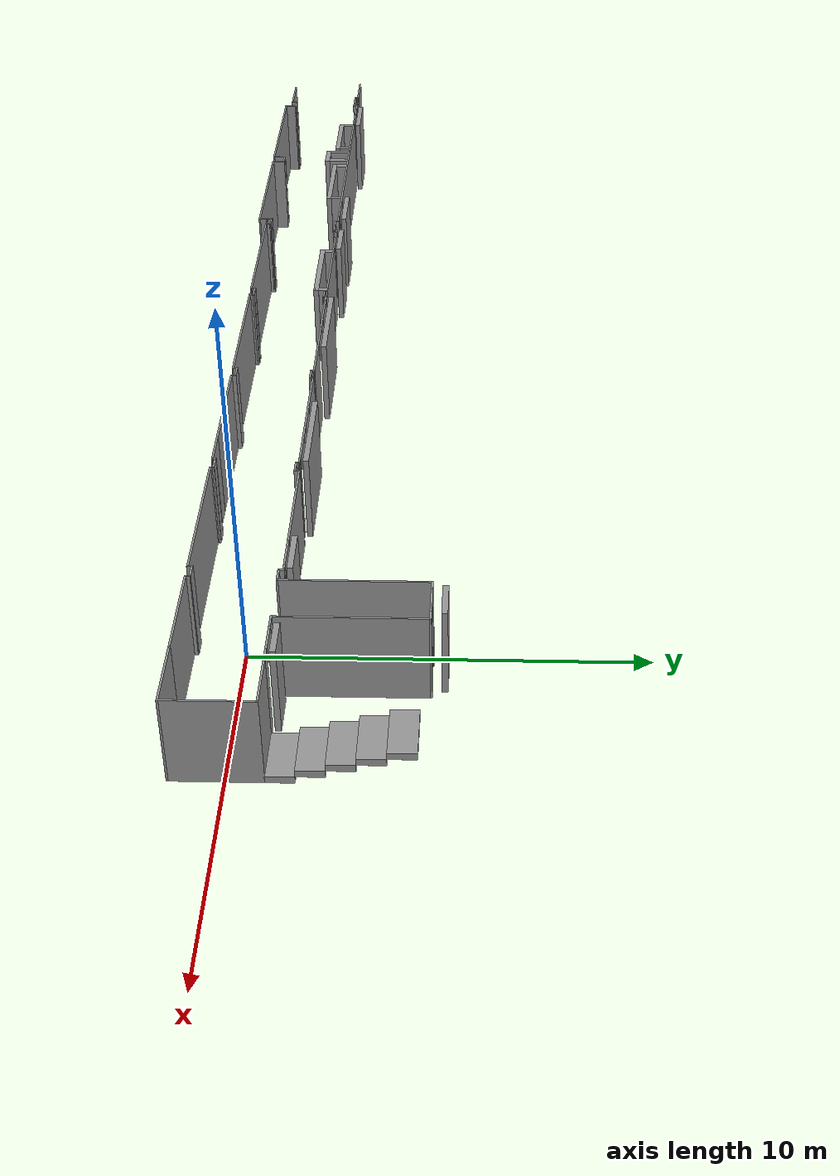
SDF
<?xml version='1.0'?>
<sdf version='1.7'>
  <model name='bot_world.world'>
    <pose>-12.0433 1.71184 0 0 -0 0</pose>
    <link name='Stairs_1'>
      <visual name='Stairs_1_Visual_0'>
        <pose>15.5557 -0.46112 0.1 0 -0 -3.14159</pose>
        <geometry>
          <box>
            <size>1.4 0.7 0.2</size>
          </box>
        </geometry>
        <material>
          <script>
            <uri>file://media/materials/scripts/gazebo.material</uri>
            <name>Gazebo/Grey</name>
          </script>
          <ambient>1 1 1 1</ambient>
        </material>
        <meta>
          <layer>0</layer>
        </meta>
      </visual>
      <collision name='Stairs_1_Collision_0'>
        <geometry>
          <box>
            <size>1.4 0.7 0.2</size>
          </box>
        </geometry>
        <pose>15.5557 -0.46112 0.1 0 -0 -3.14159</pose>
      </collision>
      <visual name='Stairs_1_Visual_1'>
        <pose>15.5557 0.23888 0.3 0 -0 -3.14159</pose>
        <geometry>
          <box>
            <size>1.4 0.7 0.2</size>
          </box>
        </geometry>
        <material>
          <script>
            <uri>file://media/materials/scripts/gazebo.material</uri>
            <name>Gazebo/Grey</name>
          </script>
          <ambient>1 1 1 1</ambient>
        </material>
        <meta>
          <layer>0</layer>
        </meta>
      </visual>
      <collision name='Stairs_1_Collision_1'>
        <geometry>
          <box>
            <size>1.4 0.7 0.2</size>
          </box>
        </geometry>
        <pose>15.5557 0.23888 0.3 0 -0 -3.14159</pose>
      </collision>
      <visual name='Stairs_1_Visual_2'>
        <pose>15.5557 0.93888 0.5 0 -0 -3.14159</pose>
        <geometry>
          <box>
            <size>1.4 0.7 0.2</size>
          </box>
        </geometry>
        <material>
          <script>
            <uri>file://media/materials/scripts/gazebo.material</uri>
            <name>Gazebo/Grey</name>
          </script>
          <ambient>1 1 1 1</ambient>
        </material>
        <meta>
          <layer>0</layer>
        </meta>
      </visual>
      <collision name='Stairs_1_Collision_2'>
        <geometry>
          <box>
            <size>1.4 0.7 0.2</size>
          </box>
        </geometry>
        <pose>15.5557 0.93888 0.5 0 -0 -3.14159</pose>
      </collision>
      <visual name='Stairs_1_Visual_3'>
        <pose>15.5557 1.63888 0.7 0 -0 -3.14159</pose>
        <geometry>
          <box>
            <size>1.4 0.7 0.2</size>
          </box>
        </geometry>
        <material>
          <script>
            <uri>file://media/materials/scripts/gazebo.material</uri>
            <name>Gazebo/Grey</name>
          </script>
          <ambient>1 1 1 1</ambient>
        </material>
        <meta>
          <layer>0</layer>
        </meta>
      </visual>
      <collision name='Stairs_1_Collision_3'>
        <geometry>
          <box>
            <size>1.4 0.7 0.2</size>
          </box>
        </geometry>
        <pose>15.5557 1.63888 0.7 0 -0 -3.14159</pose>
      </collision>
      <visual name='Stairs_1_Visual_4'>
        <pose>15.5557 2.33888 0.9 0 -0 -3.14159</pose>
        <geometry>
          <box>
            <size>1.4 0.7 0.2</size>
          </box>
        </geometry>
        <material>
          <script>
            <uri>file://media/materials/scripts/gazebo.material</uri>
            <name>Gazebo/Grey</name>
          </script>
          <ambient>1 1 1 1</ambient>
        </material>
        <meta>
          <layer>0</layer>
        </meta>
      </visual>
      <collision name='Stairs_1_Collision_4'>
        <geometry>
          <box>
            <size>1.4 0.7 0.2</size>
          </box>
        </geometry>
        <pose>15.5557 2.33888 0.9 0 -0 -3.14159</pose>
      </collision>
    </link>
    <link name='Wall_11'>
      <collision name='Wall_11_Collision'>
        <geometry>
          <box>
            <size>2.25963 0.05 2.5</size>
          </box>
        </geometry>
        <pose>0 0 1.25 0 -0 0</pose>
      </collision>
      <visual name='Wall_11_Visual'>
        <pose>0 0 1.25 0 -0 0</pose>
        <geometry>
          <box>
            <size>2.25963 0.05 2.5</size>
          </box>
        </geometry>
        <material>
          <script>
            <uri>file://media/materials/scripts/gazebo.material</uri>
            <name>Gazebo/Grey</name>
          </script>
          <ambient>1 1 1 1</ambient>
        </material>
        <meta>
          <layer>0</layer>
        </meta>
      </visual>
      <pose>16.2303 -1.92884 0 0 -0 -1.5708</pose>
    </link>
    <link name='Wall_115'>
      <collision name='Wall_115_Collision'>
        <geometry>
          <box>
            <size>3.06 0.05 2.5</size>
          </box>
        </geometry>
        <pose>0 0 1.25 0 -0 0</pose>
      </collision>
      <visual name='Wall_115_Visual'>
        <pose>0 0 1.25 0 -0 0</pose>
        <geometry>
          <box>
            <size>3.06 0.05 2.5</size>
          </box>
        </geometry>
        <material>
          <script>
            <uri>file://media/materials/scripts/gazebo.material</uri>
            <name>Gazebo/Grey</name>
          </script>
          <ambient>1 1 1 1</ambient>
        </material>
        <meta>
          <layer>0</layer>
        </meta>
      </visual>
      <pose>4.74433 -3.02584 0 0 -0 3.14159</pose>
    </link>
    <link name='Wall_117'>
      <collision name='Wall_117_Collision'>
        <geometry>
          <box>
            <size>0.16031 0.05 2.5</size>
          </box>
        </geometry>
        <pose>0 0 1.25 0 -0 0</pose>
      </collision>
      <visual name='Wall_117_Visual'>
        <pose>0 0 1.25 0 -0 0</pose>
        <geometry>
          <box>
            <size>0.16031 0.05 2.5</size>
          </box>
        </geometry>
        <material>
          <script>
            <uri>file://media/materials/scripts/gazebo.material</uri>
            <name>Gazebo/Grey</name>
          </script>
          <ambient>1 1 1 1</ambient>
        </material>
        <meta>
          <layer>0</layer>
        </meta>
      </visual>
      <pose>3.23963 -2.97069 0 0 -0 1.56535</pose>
    </link>
    <link name='Wall_118'>
      <collision name='Wall_118_Collision'>
        <geometry>
          <box>
            <size>0.42 0.05 2.5</size>
          </box>
        </geometry>
        <pose>0 0 1.25 0 -0 0</pose>
      </collision>
      <visual name='Wall_118_Visual'>
        <pose>0 0 1.25 0 -0 0</pose>
        <geometry>
          <box>
            <size>0.42 0.05 2.5</size>
          </box>
        </geometry>
        <material>
          <script>
            <uri>file://media/materials/scripts/gazebo.material</uri>
            <name>Gazebo/Grey</name>
          </script>
          <ambient>1 1 1 1</ambient>
        </material>
        <meta>
          <layer>0</layer>
        </meta>
      </visual>
      <pose>3.05433 -2.91433 0 0 -0 3.14159</pose>
    </link>
    <link name='Wall_119'>
      <collision name='Wall_119_Collision'>
        <geometry>
          <box>
            <size>0.16031 0.05 2.5</size>
          </box>
        </geometry>
        <pose>0 0 1.25 0 -0 0</pose>
      </collision>
      <visual name='Wall_119_Visual'>
        <pose>0 0 1.25 0 -0 0</pose>
        <geometry>
          <box>
            <size>0.16031 0.05 2.5</size>
          </box>
        </geometry>
        <material>
          <script>
            <uri>file://media/materials/scripts/gazebo.material</uri>
            <name>Gazebo/Grey</name>
          </script>
          <ambient>1 1 1 1</ambient>
        </material>
        <meta>
          <layer>0</layer>
        </meta>
      </visual>
      <pose>2.86963 -2.97069 0 0 -0 -1.57624</pose>
    </link>
    <link name='Wall_120'>
      <collision name='Wall_120_Collision'>
        <geometry>
          <box>
            <size>4.06 0.05 2.5</size>
          </box>
        </geometry>
        <pose>0 0 1.25 0 -0 0</pose>
      </collision>
      <visual name='Wall_120_Visual'>
        <pose>0 0 1.25 0 -0 0</pose>
        <geometry>
          <box>
            <size>4.06 0.05 2.5</size>
          </box>
        </geometry>
        <material>
          <script>
            <uri>file://media/materials/scripts/gazebo.material</uri>
            <name>Gazebo/Grey</name>
          </script>
          <ambient>1 1 1 1</ambient>
        </material>
        <meta>
          <layer>0</layer>
        </meta>
      </visual>
      <pose>0.864333 -3.02584 0 0 -0 -3.14159</pose>
    </link>
    <link name='Wall_122'>
      <collision name='Wall_122_Collision'>
        <geometry>
          <box>
            <size>0.159317 0.05 2.5</size>
          </box>
        </geometry>
        <pose>0 0 1.25 0 -0 0</pose>
      </collision>
      <visual name='Wall_122_Visual'>
        <pose>0 0 1.25 0 -0 0</pose>
        <geometry>
          <box>
            <size>0.159317 0.05 2.5</size>
          </box>
        </geometry>
        <material>
          <script>
            <uri>file://media/materials/scripts/gazebo.material</uri>
            <name>Gazebo/Grey</name>
          </script>
          <ambient>1 1 1 1</ambient>
        </material>
        <meta>
          <layer>0</layer>
        </meta>
      </visual>
      <pose>-1.14097 -2.9715 0 0 -0 1.57635</pose>
    </link>
    <link name='Wall_123'>
      <collision name='Wall_123_Collision'>
        <geometry>
          <box>
            <size>0.42 0.05 2.5</size>
          </box>
        </geometry>
        <pose>0 0 1.25 0 -0 0</pose>
      </collision>
      <visual name='Wall_123_Visual'>
        <pose>0 0 1.25 0 -0 0</pose>
        <geometry>
          <box>
            <size>0.42 0.05 2.5</size>
          </box>
        </geometry>
        <material>
          <script>
            <uri>file://media/materials/scripts/gazebo.material</uri>
            <name>Gazebo/Grey</name>
          </script>
          <ambient>1 1 1 1</ambient>
        </material>
        <meta>
          <layer>0</layer>
        </meta>
      </visual>
      <pose>-1.32567 -2.91717 0 0 -0 3.14159</pose>
    </link>
    <link name='Wall_124'>
      <collision name='Wall_124_Collision'>
        <geometry>
          <box>
            <size>0.15685 0.05 2.5</size>
          </box>
        </geometry>
        <pose>0 0 1.25 0 -0 0</pose>
      </collision>
      <visual name='Wall_124_Visual'>
        <pose>0 0 1.25 0 -0 0</pose>
        <geometry>
          <box>
            <size>0.15685 0.05 2.5</size>
          </box>
        </geometry>
        <material>
          <script>
            <uri>file://media/materials/scripts/gazebo.material</uri>
            <name>Gazebo/Grey</name>
          </script>
          <ambient>1 1 1 1</ambient>
        </material>
        <meta>
          <layer>0</layer>
        </meta>
      </visual>
      <pose>-1.51097 -2.97059 0 0 -0 -1.56515</pose>
    </link>
    <link name='Wall_125'>
      <collision name='Wall_125_Collision'>
        <geometry>
          <box>
            <size>4.08 0.05 2.5</size>
          </box>
        </geometry>
        <pose>0 0 1.25 0 -0 0</pose>
      </collision>
      <visual name='Wall_125_Visual'>
        <pose>0 0 1.25 0 -0 0</pose>
        <geometry>
          <box>
            <size>4.08 0.05 2.5</size>
          </box>
        </geometry>
        <material>
          <script>
            <uri>file://media/materials/scripts/gazebo.material</uri>
            <name>Gazebo/Grey</name>
          </script>
          <ambient>1 1 1 1</ambient>
        </material>
        <meta>
          <layer>0</layer>
        </meta>
      </visual>
      <pose>-3.52567 -3.02493 0 0 -0 3.14159</pose>
    </link>
    <link name='Wall_127'>
      <collision name='Wall_127_Collision'>
        <geometry>
          <box>
            <size>0.189791 0.05 2.5</size>
          </box>
        </geometry>
        <pose>0 0 1.25 0 -0 0</pose>
      </collision>
      <visual name='Wall_127_Visual'>
        <pose>0 0 1.25 0 -0 0</pose>
        <geometry>
          <box>
            <size>0.189791 0.05 2.5</size>
          </box>
        </geometry>
        <material>
          <script>
            <uri>file://media/materials/scripts/gazebo.material</uri>
            <name>Gazebo/Grey</name>
          </script>
          <ambient>1 1 1 1</ambient>
        </material>
        <meta>
          <layer>0</layer>
        </meta>
      </visual>
      <pose>-5.54044 -2.95432 0 0 -0 1.56758</pose>
    </link>
    <link name='Wall_128'>
      <collision name='Wall_128_Collision'>
        <geometry>
          <box>
            <size>0.39 0.05 2.5</size>
          </box>
        </geometry>
        <pose>0 0 1.25 0 -0 0</pose>
      </collision>
      <visual name='Wall_128_Visual'>
        <pose>0 0 1.25 0 -0 0</pose>
        <geometry>
          <box>
            <size>0.39 0.05 2.5</size>
          </box>
        </geometry>
        <material>
          <script>
            <uri>file://media/materials/scripts/gazebo.material</uri>
            <name>Gazebo/Grey</name>
          </script>
          <ambient>1 1 1 1</ambient>
        </material>
        <meta>
          <layer>0</layer>
        </meta>
      </visual>
      <pose>-5.71022 -2.88462 0 0 -0 3.14159</pose>
    </link>
    <link name='Wall_129'>
      <collision name='Wall_129_Collision'>
        <geometry>
          <box>
            <size>0.188127 0.05 2.5</size>
          </box>
        </geometry>
        <pose>0 0 1.25 0 -0 0</pose>
      </collision>
      <visual name='Wall_129_Visual'>
        <pose>0 0 1.25 0 -0 0</pose>
        <geometry>
          <box>
            <size>0.188127 0.05 2.5</size>
          </box>
        </geometry>
        <material>
          <script>
            <uri>file://media/materials/scripts/gazebo.material</uri>
            <name>Gazebo/Grey</name>
          </script>
          <ambient>1 1 1 1</ambient>
        </material>
        <meta>
          <layer>0</layer>
        </meta>
      </visual>
      <pose>-5.88004 -2.95398 0 0 -0 -1.56823</pose>
    </link>
    <link name='Wall_13'>
      <collision name='Wall_13_Collision'>
        <geometry>
          <box>
            <size>1.4 0.05 2.5</size>
          </box>
        </geometry>
        <pose>0 0 1.25 0 -0 0</pose>
      </collision>
      <visual name='Wall_13_Visual'>
        <pose>0 0 1.25 0 -0 0</pose>
        <geometry>
          <box>
            <size>1.4 0.05 2.5</size>
          </box>
        </geometry>
        <material>
          <script>
            <uri>file://media/materials/scripts/gazebo.material</uri>
            <name>Gazebo/Grey</name>
          </script>
          <ambient>1 1 1 1</ambient>
        </material>
        <meta>
          <layer>0</layer>
        </meta>
      </visual>
      <pose>15.5553 -0.823841 0 0 -0 3.14159</pose>
    </link>
    <link name='Wall_130'>
      <collision name='Wall_130_Collision'>
        <geometry>
          <box>
            <size>0.29 0.05 2.5</size>
          </box>
        </geometry>
        <pose>0 0 1.25 0 -0 0</pose>
      </collision>
      <visual name='Wall_130_Visual'>
        <pose>0 0 1.25 0 -0 0</pose>
        <geometry>
          <box>
            <size>0.29 0.05 2.5</size>
          </box>
        </geometry>
        <material>
          <script>
            <uri>file://media/materials/scripts/gazebo.material</uri>
            <name>Gazebo/Grey</name>
          </script>
          <ambient>1 1 1 1</ambient>
        </material>
        <meta>
          <layer>0</layer>
        </meta>
      </visual>
      <pose>-5.87986 -3.14334 0 0 -0 -1.5708</pose>
    </link>
    <link name='Wall_131'>
      <collision name='Wall_131_Collision'>
        <geometry>
          <box>
            <size>4.03 0 2.5</size>
          </box>
        </geometry>
        <pose>0 0 1.25 0 -0 0</pose>
      </collision>
      <visual name='Wall_131_Visual'>
        <pose>0 0 1.25 0 -0 0</pose>
        <geometry>
          <box>
            <size>4.03 0 2.5</size>
          </box>
        </geometry>
        <material>
          <script>
            <uri>file://media/materials/scripts/gazebo.material</uri>
            <name>Gazebo/Grey</name>
          </script>
          <ambient>1 1 1 1</ambient>
        </material>
        <meta>
          <layer>0</layer>
        </meta>
      </visual>
      <pose>-7.89476 -3.26309 0 0 -0 3.14147</pose>
    </link>
    <link name='Wall_133'>
      <collision name='Wall_133_Collision'>
        <geometry>
          <box>
            <size>4.08 0.05 2.5</size>
          </box>
        </geometry>
        <pose>0 0 1.25 0 -0 0</pose>
      </collision>
      <visual name='Wall_133_Visual'>
        <pose>0 0 1.25 0 -0 0</pose>
        <geometry>
          <box>
            <size>4.08 0.05 2.5</size>
          </box>
        </geometry>
        <material>
          <script>
            <uri>file://media/materials/scripts/gazebo.material</uri>
            <name>Gazebo/Grey</name>
          </script>
          <ambient>1 1 1 1</ambient>
        </material>
        <meta>
          <layer>0</layer>
        </meta>
      </visual>
      <pose>-7.89476 -3.26309 0 0 -0 3.14147</pose>
    </link>
    <link name='Wall_135'>
      <collision name='Wall_135_Collision'>
        <geometry>
          <box>
            <size>0.399503 0.05 2.5</size>
          </box>
        </geometry>
        <pose>0 0 1.25 0 -0 0</pose>
      </collision>
      <visual name='Wall_135_Visual'>
        <pose>0 0 1.25 0 -0 0</pose>
        <geometry>
          <box>
            <size>0.399503 0.05 2.5</size>
          </box>
        </geometry>
        <material>
          <script>
            <uri>file://media/materials/scripts/gazebo.material</uri>
            <name>Gazebo/Grey</name>
          </script>
          <ambient>1 1 1 1</ambient>
        </material>
        <meta>
          <layer>0</layer>
        </meta>
      </visual>
      <pose>-9.90967 -3.08784 0 0 -0 1.5708</pose>
    </link>
    <link name='Wall_136'>
      <collision name='Wall_136_Collision'>
        <geometry>
          <box>
            <size>0.39 0.05 2.5</size>
          </box>
        </geometry>
        <pose>0 0 1.25 0 -0 0</pose>
      </collision>
      <visual name='Wall_136_Visual'>
        <pose>0 0 1.25 0 -0 0</pose>
        <geometry>
          <box>
            <size>0.39 0.05 2.5</size>
          </box>
        </geometry>
        <material>
          <script>
            <uri>file://media/materials/scripts/gazebo.material</uri>
            <name>Gazebo/Grey</name>
          </script>
          <ambient>1 1 1 1</ambient>
        </material>
        <meta>
          <layer>0</layer>
        </meta>
      </visual>
      <pose>-10.0797 -2.91284 0 0 -0 3.14159</pose>
    </link>
    <link name='Wall_137'>
      <collision name='Wall_137_Collision'>
        <geometry>
          <box>
            <size>0.4 0.05 2.5</size>
          </box>
        </geometry>
        <pose>0 0 1.25 0 -0 0</pose>
      </collision>
      <visual name='Wall_137_Visual'>
        <pose>0 0 1.25 0 -0 0</pose>
        <geometry>
          <box>
            <size>0.4 0.05 2.5</size>
          </box>
        </geometry>
        <material>
          <script>
            <uri>file://media/materials/scripts/gazebo.material</uri>
            <name>Gazebo/Grey</name>
          </script>
          <ambient>1 1 1 1</ambient>
        </material>
        <meta>
          <layer>0</layer>
        </meta>
      </visual>
      <pose>-10.2497 -3.08784 0 0 -0 -1.5708</pose>
    </link>
    <link name='Wall_138'>
      <collision name='Wall_138_Collision'>
        <geometry>
          <box>
            <size>4.08 0.05 2.5</size>
          </box>
        </geometry>
        <pose>0 0 1.25 0 -0 0</pose>
      </collision>
      <visual name='Wall_138_Visual'>
        <pose>0 0 1.25 0 -0 0</pose>
        <geometry>
          <box>
            <size>4.08 0.05 2.5</size>
          </box>
        </geometry>
        <material>
          <script>
            <uri>file://media/materials/scripts/gazebo.material</uri>
            <name>Gazebo/Grey</name>
          </script>
          <ambient>1 1 1 1</ambient>
        </material>
        <meta>
          <layer>0</layer>
        </meta>
      </visual>
      <pose>-12.2647 -3.26284 0 0 -0 3.14159</pose>
    </link>
    <link name='Wall_140'>
      <collision name='Wall_140_Collision'>
        <geometry>
          <box>
            <size>0.39 0.05 2.5</size>
          </box>
        </geometry>
        <pose>0 0 1.25 0 -0 0</pose>
      </collision>
      <visual name='Wall_140_Visual'>
        <pose>0 0 1.25 0 -0 0</pose>
        <geometry>
          <box>
            <size>0.39 0.05 2.5</size>
          </box>
        </geometry>
        <material>
          <script>
            <uri>file://media/materials/scripts/gazebo.material</uri>
            <name>Gazebo/Grey</name>
          </script>
          <ambient>1 1 1 1</ambient>
        </material>
        <meta>
          <layer>0</layer>
        </meta>
      </visual>
      <pose>-14.2797 -3.09284 0 0 -0 1.5708</pose>
    </link>
    <link name='Wall_141'>
      <collision name='Wall_141_Collision'>
        <geometry>
          <box>
            <size>0.39 0.05 2.5</size>
          </box>
        </geometry>
        <pose>0 0 1.25 0 -0 0</pose>
      </collision>
      <visual name='Wall_141_Visual'>
        <pose>0 0 1.25 0 -0 0</pose>
        <geometry>
          <box>
            <size>0.39 0.05 2.5</size>
          </box>
        </geometry>
        <material>
          <script>
            <uri>file://media/materials/scripts/gazebo.material</uri>
            <name>Gazebo/Grey</name>
          </script>
          <ambient>1 1 1 1</ambient>
        </material>
        <meta>
          <layer>0</layer>
        </meta>
      </visual>
      <pose>-14.4497 -2.92284 0 0 -0 3.14159</pose>
    </link>
    <link name='Wall_143'>
      <collision name='Wall_143_Collision'>
        <geometry>
          <box>
            <size>0.19 0.05 2.5</size>
          </box>
        </geometry>
        <pose>0 0 1.25 0 -0 0</pose>
      </collision>
      <visual name='Wall_143_Visual'>
        <pose>0 0 1.25 0 -0 0</pose>
        <geometry>
          <box>
            <size>0.19 0.05 2.5</size>
          </box>
        </geometry>
        <material>
          <script>
            <uri>file://media/materials/scripts/gazebo.material</uri>
            <name>Gazebo/Grey</name>
          </script>
          <ambient>1 1 1 1</ambient>
        </material>
        <meta>
          <layer>0</layer>
        </meta>
      </visual>
      <pose>-14.6197 -2.99284 0 0 -0 -1.5708</pose>
    </link>
    <link name='Wall_144'>
      <collision name='Wall_144_Collision'>
        <geometry>
          <box>
            <size>1.25 0.05 2.5</size>
          </box>
        </geometry>
        <pose>0 0 1.25 0 -0 0</pose>
      </collision>
      <visual name='Wall_144_Visual'>
        <pose>0 0 1.25 0 -0 0</pose>
        <geometry>
          <box>
            <size>1.25 0.05 2.5</size>
          </box>
        </geometry>
        <material>
          <script>
            <uri>file://media/materials/scripts/gazebo.material</uri>
            <name>Gazebo/Grey</name>
          </script>
          <ambient>1 1 1 1</ambient>
        </material>
        <meta>
          <layer>0</layer>
        </meta>
      </visual>
      <pose>-15.2197 -3.06284 0 0 -0 3.14159</pose>
    </link>
    <link name='Wall_146'>
      <collision name='Wall_146_Collision'>
        <geometry>
          <box>
            <size>0.42 0.15 2.5</size>
          </box>
        </geometry>
        <pose>0 0 1.25 0 -0 0</pose>
      </collision>
      <visual name='Wall_146_Visual'>
        <pose>0 0 1.25 0 -0 0</pose>
        <geometry>
          <box>
            <size>0.42 0.15 2.5</size>
          </box>
        </geometry>
        <material>
          <script>
            <uri>file://media/materials/scripts/gazebo.material</uri>
            <name>Gazebo/Grey</name>
          </script>
          <ambient>1 1 1 1</ambient>
        </material>
        <meta>
          <layer>0</layer>
        </meta>
      </visual>
      <pose>-3.80107 -0.936792 0 0 -0 -1.5708</pose>
    </link>
    <link name='Wall_147'>
      <collision name='Wall_147_Collision'>
        <geometry>
          <box>
            <size>2.44162 0.15 2.5</size>
          </box>
        </geometry>
        <pose>0 0 1.25 0 -0 0</pose>
      </collision>
      <visual name='Wall_147_Visual'>
        <pose>0 0 1.25 0 -0 0</pose>
        <geometry>
          <box>
            <size>2.44162 0.15 2.5</size>
          </box>
        </geometry>
        <material>
          <script>
            <uri>file://media/materials/scripts/gazebo.material</uri>
            <name>Gazebo/Grey</name>
          </script>
          <ambient>1 1 1 1</ambient>
        </material>
        <meta>
          <layer>0</layer>
        </meta>
      </visual>
      <pose>-2.65422 -1.07154 0 0 -0 0.000218</pose>
    </link>
    <link name='Wall_148'>
      <collision name='Wall_148_Collision'>
        <geometry>
          <box>
            <size>0.42 0.15 2.5</size>
          </box>
        </geometry>
        <pose>0 0 1.25 0 -0 0</pose>
      </collision>
      <visual name='Wall_148_Visual'>
        <pose>0 0 1.25 0 -0 0</pose>
        <geometry>
          <box>
            <size>0.42 0.15 2.5</size>
          </box>
        </geometry>
        <material>
          <script>
            <uri>file://media/materials/scripts/gazebo.material</uri>
            <name>Gazebo/Grey</name>
          </script>
          <ambient>1 1 1 1</ambient>
        </material>
        <meta>
          <layer>0</layer>
        </meta>
      </visual>
      <pose>-1.51023 -0.934476 0 0 -0 1.5708</pose>
    </link>
    <link name='Wall_15'>
      <pose>14.1353 -0.823841 0 0 -0 3.14159</pose>
      <visual name='Wall_15_Visual_0'>
        <pose>-0.569151 0 1.25 0 -0 0</pose>
        <geometry>
          <box>
            <size>0.401698 0.05 2.5</size>
          </box>
        </geometry>
        <material>
          <script>
            <uri>file://media/materials/scripts/gazebo.material</uri>
            <name>Gazebo/Grey</name>
          </script>
          <ambient>1 1 1 1</ambient>
        </material>
        <meta>
          <layer>0</layer>
        </meta>
      </visual>
      <collision name='Wall_15_Collision_0'>
        <geometry>
          <box>
            <size>0.401698 0.05 2.5</size>
          </box>
        </geometry>
        <pose>-0.569151 0 1.25 0 -0 0</pose>
      </collision>
      <visual name='Wall_15_Visual_1'>
        <pose>0.590849 0 1.25 0 -0 0</pose>
        <geometry>
          <box>
            <size>0.358302 0.05 2.5</size>
          </box>
        </geometry>
        <material>
          <script>
            <uri>file://media/materials/scripts/gazebo.material</uri>
            <name>Gazebo/Grey</name>
          </script>
          <ambient>1 1 1 1</ambient>
        </material>
        <meta>
          <layer>0</layer>
        </meta>
      </visual>
      <collision name='Wall_15_Collision_1'>
        <geometry>
          <box>
            <size>0.358302 0.05 2.5</size>
          </box>
        </geometry>
        <pose>0.590849 0 1.25 0 -0 0</pose>
      </collision>
      <visual name='Wall_15_Visual_2'>
        <pose>0.021698 0 2.25 0 -0 0</pose>
        <geometry>
          <box>
            <size>0.78 0.05 0.5</size>
          </box>
        </geometry>
        <material>
          <script>
            <uri>file://media/materials/scripts/gazebo.material</uri>
            <name>Gazebo/Grey</name>
          </script>
          <ambient>1 1 1 1</ambient>
        </material>
        <meta>
          <layer>0</layer>
        </meta>
      </visual>
      <collision name='Wall_15_Collision_2'>
        <geometry>
          <box>
            <size>0.78 0.05 0.5</size>
          </box>
        </geometry>
        <pose>0.021698 0 2.25 0 -0 0</pose>
      </collision>
    </link>
    <link name='Wall_153'>
      <collision name='Wall_153_Collision'>
        <geometry>
          <box>
            <size>2.44 0.15 2.5</size>
          </box>
        </geometry>
        <pose>0 0 1.25 0 -0 0</pose>
      </collision>
      <visual name='Wall_153_Visual'>
        <pose>0 0 1.25 0 -0 0</pose>
        <geometry>
          <box>
            <size>2.44 0.15 2.5</size>
          </box>
        </geometry>
        <material>
          <script>
            <uri>file://media/materials/scripts/gazebo.material</uri>
            <name>Gazebo/Grey</name>
          </script>
          <ambient>1 1 1 1</ambient>
        </material>
        <meta>
          <layer>0</layer>
        </meta>
      </visual>
      <pose>-8.49434 -1.15782 0 0 -0 0</pose>
    </link>
    <link name='Wall_155'>
      <collision name='Wall_155_Collision'>
        <geometry>
          <box>
            <size>1.88 0.15 2.5</size>
          </box>
        </geometry>
        <pose>0 0 1.25 0 -0 0</pose>
      </collision>
      <visual name='Wall_155_Visual'>
        <pose>0 0 1.25 0 -0 0</pose>
        <geometry>
          <box>
            <size>1.88 0.15 2.5</size>
          </box>
        </geometry>
        <material>
          <script>
            <uri>file://media/materials/scripts/gazebo.material</uri>
            <name>Gazebo/Grey</name>
          </script>
          <ambient>1 1 1 1</ambient>
        </material>
        <meta>
          <layer>0</layer>
        </meta>
      </visual>
      <pose>-11.852 -1.1527 0 0 -0 0</pose>
    </link>
    <link name='Wall_157'>
      <collision name='Wall_157_Collision'>
        <geometry>
          <box>
            <size>0.74 0.15 2.5</size>
          </box>
        </geometry>
        <pose>0 0 1.25 0 -0 0</pose>
      </collision>
      <visual name='Wall_157_Visual'>
        <pose>0 0 1.25 0 -0 0</pose>
        <geometry>
          <box>
            <size>0.74 0.15 2.5</size>
          </box>
        </geometry>
        <material>
          <script>
            <uri>file://media/materials/scripts/gazebo.material</uri>
            <name>Gazebo/Grey</name>
          </script>
          <ambient>1 1 1 1</ambient>
        </material>
        <meta>
          <layer>0</layer>
        </meta>
      </visual>
      <pose>-10.3561 -1.43327 0 0 -0 0</pose>
    </link>
    <link name='Wall_159'>
      <collision name='Wall_159_Collision'>
        <geometry>
          <box>
            <size>0.6 0.15 2.5</size>
          </box>
        </geometry>
        <pose>0 0 1.25 0 -0 0</pose>
      </collision>
      <visual name='Wall_159_Visual'>
        <pose>0 0 1.25 0 -0 0</pose>
        <geometry>
          <box>
            <size>0.6 0.15 2.5</size>
          </box>
        </geometry>
        <material>
          <script>
            <uri>file://media/materials/scripts/gazebo.material</uri>
            <name>Gazebo/Grey</name>
          </script>
          <ambient>1 1 1 1</ambient>
        </material>
        <meta>
          <layer>0</layer>
        </meta>
      </visual>
      <pose>-10.6528 -1.06038 0 0 -0 -1.5708</pose>
    </link>
    <link name='Wall_161'>
      <collision name='Wall_161_Collision'>
        <geometry>
          <box>
            <size>0.34 0.15 2.5</size>
          </box>
        </geometry>
        <pose>0 0 1.25 0 -0 0</pose>
      </collision>
      <visual name='Wall_161_Visual'>
        <pose>0 0 1.25 0 -0 0</pose>
        <geometry>
          <box>
            <size>0.34 0.15 2.5</size>
          </box>
        </geometry>
        <material>
          <script>
            <uri>file://media/materials/scripts/gazebo.material</uri>
            <name>Gazebo/Grey</name>
          </script>
          <ambient>1 1 1 1</ambient>
        </material>
        <meta>
          <layer>0</layer>
        </meta>
      </visual>
      <pose>-12.7201 -0.915227 0 0 -0 -1.5708</pose>
    </link>
    <link name='Wall_163'>
      <collision name='Wall_163_Collision'>
        <geometry>
          <box>
            <size>0.34 0.15 2.5</size>
          </box>
        </geometry>
        <pose>0 0 1.25 0 -0 0</pose>
      </collision>
      <visual name='Wall_163_Visual'>
        <pose>0 0 1.25 0 -0 0</pose>
        <geometry>
          <box>
            <size>0.34 0.15 2.5</size>
          </box>
        </geometry>
        <material>
          <script>
            <uri>file://media/materials/scripts/gazebo.material</uri>
            <name>Gazebo/Grey</name>
          </script>
          <ambient>1 1 1 1</ambient>
        </material>
        <meta>
          <layer>0</layer>
        </meta>
      </visual>
      <pose>-7.36079 -0.926538 0 0 -0 -1.5708</pose>
    </link>
    <link name='Wall_165'>
      <collision name='Wall_165_Collision'>
        <geometry>
          <box>
            <size>0.6 0.15 2.5</size>
          </box>
        </geometry>
        <pose>0 0 1.25 0 -0 0</pose>
      </collision>
      <visual name='Wall_165_Visual'>
        <pose>0 0 1.25 0 -0 0</pose>
        <geometry>
          <box>
            <size>0.6 0.15 2.5</size>
          </box>
        </geometry>
        <material>
          <script>
            <uri>file://media/materials/scripts/gazebo.material</uri>
            <name>Gazebo/Grey</name>
          </script>
          <ambient>1 1 1 1</ambient>
        </material>
        <meta>
          <layer>0</layer>
        </meta>
      </visual>
      <pose>-10.0621 -1.06367 0 0 -0 -1.5708</pose>
    </link>
    <link name='Wall_167'>
      <collision name='Wall_167_Collision'>
        <geometry>
          <box>
            <size>0.34 0.15 2.5</size>
          </box>
        </geometry>
        <pose>0 0 1.25 0 -0 0</pose>
      </collision>
      <visual name='Wall_167_Visual'>
        <pose>0 0 1.25 0 -0 0</pose>
        <geometry>
          <box>
            <size>0.34 0.15 2.5</size>
          </box>
        </geometry>
        <material>
          <script>
            <uri>file://media/materials/scripts/gazebo.material</uri>
            <name>Gazebo/Grey</name>
          </script>
          <ambient>1 1 1 1</ambient>
        </material>
        <meta>
          <layer>0</layer>
        </meta>
      </visual>
      <pose>-10.9881 -0.924091 0 0 -0 -1.5708</pose>
    </link>
    <link name='Wall_169'>
      <collision name='Wall_169_Collision'>
        <geometry>
          <box>
            <size>0.34 0.15 2.5</size>
          </box>
        </geometry>
        <pose>0 0 1.25 0 -0 0</pose>
      </collision>
      <visual name='Wall_169_Visual'>
        <pose>0 0 1.25 0 -0 0</pose>
        <geometry>
          <box>
            <size>0.34 0.15 2.5</size>
          </box>
        </geometry>
        <material>
          <script>
            <uri>file://media/materials/scripts/gazebo.material</uri>
            <name>Gazebo/Grey</name>
          </script>
          <ambient>1 1 1 1</ambient>
        </material>
        <meta>
          <layer>0</layer>
        </meta>
      </visual>
      <pose>-9.63479 -0.920496 0 0 -0 -1.5708</pose>
    </link>
    <link name='Wall_17'>
      <collision name='Wall_17_Collision'>
        <geometry>
          <box>
            <size>1 0.15 2.5</size>
          </box>
        </geometry>
        <pose>0 0 1.25 0 -0 0</pose>
      </collision>
      <visual name='Wall_17_Visual'>
        <pose>0 0 1.25 0 -0 0</pose>
        <geometry>
          <box>
            <size>1 0.15 2.5</size>
          </box>
        </geometry>
        <material>
          <script>
            <uri>file://media/materials/scripts/gazebo.material</uri>
            <name>Gazebo/Grey</name>
          </script>
          <ambient>1 1 1 1</ambient>
        </material>
        <meta>
          <layer>0</layer>
        </meta>
      </visual>
      <pose>14.1043 -0.666199 0 0 -0 0</pose>
    </link>
    <link name='Wall_19'>
      <collision name='Wall_19_Collision'>
        <geometry>
          <box>
            <size>3.76 0.05 2.5</size>
          </box>
        </geometry>
        <pose>0 0 1.25 0 -0 0</pose>
      </collision>
      <visual name='Wall_19_Visual'>
        <pose>0 0 1.25 0 -0 0</pose>
        <geometry>
          <box>
            <size>3.76 0.05 2.5</size>
          </box>
        </geometry>
        <material>
          <script>
            <uri>file://media/materials/scripts/gazebo.material</uri>
            <name>Gazebo/Grey</name>
          </script>
          <ambient>1 1 1 1</ambient>
        </material>
        <meta>
          <layer>0</layer>
        </meta>
      </visual>
      <pose>13.3903 1.03116 0 0 -0 1.5708</pose>
    </link>
    <link name='Wall_21'>
      <pose>12.7278 2.88616 0 0 -0 3.14159</pose>
      <visual name='Wall_21_Visual_0'>
        <pose>-0.536013 0 1.25 0 -0 0</pose>
        <geometry>
          <box>
            <size>0.302974 0.05 2.5</size>
          </box>
        </geometry>
        <material>
          <script>
            <uri>file://media/materials/scripts/gazebo.material</uri>
            <name>Gazebo/Grey</name>
          </script>
          <ambient>1 1 1 1</ambient>
        </material>
        <meta>
          <layer>0</layer>
        </meta>
      </visual>
      <collision name='Wall_21_Collision_0'>
        <geometry>
          <box>
            <size>0.302974 0.05 2.5</size>
          </box>
        </geometry>
        <pose>-0.536013 0 1.25 0 -0 0</pose>
      </collision>
      <visual name='Wall_21_Visual_1'>
        <pose>0.551487 0 1.25 0 -0 0</pose>
        <geometry>
          <box>
            <size>0.272026 0.05 2.5</size>
          </box>
        </geometry>
        <material>
          <script>
            <uri>file://media/materials/scripts/gazebo.material</uri>
            <name>Gazebo/Grey</name>
          </script>
          <ambient>1 1 1 1</ambient>
        </material>
        <meta>
          <layer>0</layer>
        </meta>
      </visual>
      <collision name='Wall_21_Collision_1'>
        <geometry>
          <box>
            <size>0.272026 0.05 2.5</size>
          </box>
        </geometry>
        <pose>0.551487 0 1.25 0 -0 0</pose>
      </collision>
      <visual name='Wall_21_Visual_2'>
        <pose>0.015474 0 2.25 0 -0 0</pose>
        <geometry>
          <box>
            <size>0.8 0.05 0.5</size>
          </box>
        </geometry>
        <material>
          <script>
            <uri>file://media/materials/scripts/gazebo.material</uri>
            <name>Gazebo/Grey</name>
          </script>
          <ambient>1 1 1 1</ambient>
        </material>
        <meta>
          <layer>0</layer>
        </meta>
      </visual>
      <collision name='Wall_21_Collision_2'>
        <geometry>
          <box>
            <size>0.8 0.05 0.5</size>
          </box>
        </geometry>
        <pose>0.015474 0 2.25 0 -0 0</pose>
      </collision>
    </link>
    <link name='Wall_23'>
      <collision name='Wall_23_Collision'>
        <geometry>
          <box>
            <size>1 0.15 2.5</size>
          </box>
        </geometry>
        <pose>0 0 1.25 0 -0 0</pose>
      </collision>
      <visual name='Wall_23_Visual'>
        <pose>0 0 1.25 0 -0 0</pose>
        <geometry>
          <box>
            <size>1 0.15 2.5</size>
          </box>
        </geometry>
        <material>
          <script>
            <uri>file://media/materials/scripts/gazebo.material</uri>
            <name>Gazebo/Grey</name>
          </script>
          <ambient>1 1 1 1</ambient>
        </material>
        <meta>
          <layer>0</layer>
        </meta>
      </visual>
      <pose>12.6998 3.21334 0 0 -0 0</pose>
    </link>
    <link name='Wall_25'>
      <collision name='Wall_25_Collision'>
        <geometry>
          <box>
            <size>3.76 0.05 2.5</size>
          </box>
        </geometry>
        <pose>0 0 1.25 0 -0 0</pose>
      </collision>
      <visual name='Wall_25_Visual'>
        <pose>0 0 1.25 0 -0 0</pose>
        <geometry>
          <box>
            <size>3.76 0.05 2.5</size>
          </box>
        </geometry>
        <material>
          <script>
            <uri>file://media/materials/scripts/gazebo.material</uri>
            <name>Gazebo/Grey</name>
          </script>
          <ambient>1 1 1 1</ambient>
        </material>
        <meta>
          <layer>0</layer>
        </meta>
      </visual>
      <pose>12.0653 1.03116 0 0 -0 -1.5708</pose>
    </link>
    <link name='Wall_33'>
      <collision name='Wall_33_Collision'>
        <geometry>
          <box>
            <size>0.42 0.05 2.5</size>
          </box>
        </geometry>
        <pose>0 0 1.25 0 -0 0</pose>
      </collision>
      <visual name='Wall_33_Visual'>
        <pose>0 0 1.25 0 -0 0</pose>
        <geometry>
          <box>
            <size>0.42 0.05 2.5</size>
          </box>
        </geometry>
        <material>
          <script>
            <uri>file://media/materials/scripts/gazebo.material</uri>
            <name>Gazebo/Grey</name>
          </script>
          <ambient>1 1 1 1</ambient>
        </material>
        <meta>
          <layer>0</layer>
        </meta>
      </visual>
      <pose>11.8803 -0.823841 0 0 -0 3.14159</pose>
    </link>
    <link name='Wall_34'>
      <collision name='Wall_34_Collision'>
        <geometry>
          <box>
            <size>0.165815 0.05 2.5</size>
          </box>
        </geometry>
        <pose>0 0 1.25 0 -0 0</pose>
      </collision>
      <visual name='Wall_34_Visual'>
        <pose>0 0 1.25 0 -0 0</pose>
        <geometry>
          <box>
            <size>0.165815 0.05 2.5</size>
          </box>
        </geometry>
        <material>
          <script>
            <uri>file://media/materials/scripts/gazebo.material</uri>
            <name>Gazebo/Grey</name>
          </script>
          <ambient>1 1 1 1</ambient>
        </material>
        <meta>
          <layer>0</layer>
        </meta>
      </visual>
      <pose>11.6953 -0.765934 0 0 -0 1.57199</pose>
    </link>
    <link name='Wall_35'>
      <pose>9.68019 -0.709288 0 0 -0 -3.14097</pose>
      <visual name='Wall_35_Visual_0'>
        <pose>-1.92329 0 1.25 0 -0 0</pose>
        <geometry>
          <box>
            <size>0.233415 0.05 2.5</size>
          </box>
        </geometry>
        <material>
          <script>
            <uri>file://media/materials/scripts/gazebo.material</uri>
            <name>Gazebo/Grey</name>
          </script>
          <ambient>1 1 1 1</ambient>
        </material>
        <meta>
          <layer>0</layer>
        </meta>
      </visual>
      <collision name='Wall_35_Collision_0'>
        <geometry>
          <box>
            <size>0.233415 0.05 2.5</size>
          </box>
        </geometry>
        <pose>-1.92329 0 1.25 0 -0 0</pose>
      </collision>
      <visual name='Wall_35_Visual_1'>
        <pose>0.596708 0 1.25 0 -0 0</pose>
        <geometry>
          <box>
            <size>2.88659 0.05 2.5</size>
          </box>
        </geometry>
        <material>
          <script>
            <uri>file://media/materials/scripts/gazebo.material</uri>
            <name>Gazebo/Grey</name>
          </script>
          <ambient>1 1 1 1</ambient>
        </material>
        <meta>
          <layer>0</layer>
        </meta>
      </visual>
      <collision name='Wall_35_Collision_1'>
        <geometry>
          <box>
            <size>2.88659 0.05 2.5</size>
          </box>
        </geometry>
        <pose>0.596708 0 1.25 0 -0 0</pose>
      </collision>
      <visual name='Wall_35_Visual_2'>
        <pose>-1.32658 0 2.25 0 -0 0</pose>
        <geometry>
          <box>
            <size>0.96 0.05 0.5</size>
          </box>
        </geometry>
        <material>
          <script>
            <uri>file://media/materials/scripts/gazebo.material</uri>
            <name>Gazebo/Grey</name>
          </script>
          <ambient>1 1 1 1</ambient>
        </material>
        <meta>
          <layer>0</layer>
        </meta>
      </visual>
      <collision name='Wall_35_Collision_2'>
        <geometry>
          <box>
            <size>0.96 0.05 0.5</size>
          </box>
        </geometry>
        <pose>-1.32658 0 2.25 0 -0 0</pose>
      </collision>
    </link>
    <link name='Wall_37'>
      <collision name='Wall_37_Collision'>
        <geometry>
          <box>
            <size>1.25 0.15 2.5</size>
          </box>
        </geometry>
        <pose>0 0 1.25 0 -0 0</pose>
      </collision>
      <visual name='Wall_37_Visual'>
        <pose>0 0 1.25 0 -0 0</pose>
        <geometry>
          <box>
            <size>1.25 0.15 2.5</size>
          </box>
        </geometry>
        <material>
          <script>
            <uri>file://media/materials/scripts/gazebo.material</uri>
            <name>Gazebo/Grey</name>
          </script>
          <ambient>1 1 1 1</ambient>
        </material>
        <meta>
          <layer>0</layer>
        </meta>
      </visual>
      <pose>10.9877 -0.564022 0 0 -0 0</pose>
    </link>
    <link name='Wall_39'>
      <collision name='Wall_39_Collision'>
        <geometry>
          <box>
            <size>0.16433 0.05 2.5</size>
          </box>
        </geometry>
        <pose>0 0 1.25 0 -0 0</pose>
      </collision>
      <visual name='Wall_39_Visual'>
        <pose>0 0 1.25 0 -0 0</pose>
        <geometry>
          <box>
            <size>0.16433 0.05 2.5</size>
          </box>
        </geometry>
        <material>
          <script>
            <uri>file://media/materials/scripts/gazebo.material</uri>
            <name>Gazebo/Grey</name>
          </script>
          <ambient>1 1 1 1</ambient>
        </material>
        <meta>
          <layer>0</layer>
        </meta>
      </visual>
      <pose>7.6653 -0.767445 0 0 -0 -1.56897</pose>
    </link>
    <link name='Wall_40'>
      <collision name='Wall_40_Collision'>
        <geometry>
          <box>
            <size>0.408421 0.05 2.5</size>
          </box>
        </geometry>
        <pose>0 0 1.25 0 -0 0</pose>
      </collision>
      <visual name='Wall_40_Visual'>
        <pose>0 0 1.25 0 -0 0</pose>
        <geometry>
          <box>
            <size>0.408421 0.05 2.5</size>
          </box>
        </geometry>
        <material>
          <script>
            <uri>file://media/materials/scripts/gazebo.material</uri>
            <name>Gazebo/Grey</name>
          </script>
          <ambient>1 1 1 1</ambient>
        </material>
        <meta>
          <layer>0</layer>
        </meta>
      </visual>
      <pose>7.48596 -0.824491 0 0 -0 -3.14076</pose>
    </link>
    <link name='Wall_41'>
      <collision name='Wall_41_Collision'>
        <geometry>
          <box>
            <size>0.13 0.05 2.5</size>
          </box>
        </geometry>
        <pose>0 0 1.25 0 -0 0</pose>
      </collision>
      <visual name='Wall_41_Visual'>
        <pose>0 0 1.25 0 -0 0</pose>
        <geometry>
          <box>
            <size>0.13 0.05 2.5</size>
          </box>
        </geometry>
        <material>
          <script>
            <uri>file://media/materials/scripts/gazebo.material</uri>
            <name>Gazebo/Grey</name>
          </script>
          <ambient>1 1 1 1</ambient>
        </material>
        <meta>
          <layer>0</layer>
        </meta>
      </visual>
      <pose>7.30722 -0.78464 0 0 -0 1.56661</pose>
    </link>
    <link name='Wall_43'>
      <pose>5.31239 -0.744641 0 0 -0 3.14159</pose>
      <visual name='Wall_43_Visual_0'>
        <pose>-1.90075 0 1.25 0 -0 0</pose>
        <geometry>
          <box>
            <size>0.238496 0.05 2.5</size>
          </box>
        </geometry>
        <material>
          <script>
            <uri>file://media/materials/scripts/gazebo.material</uri>
            <name>Gazebo/Grey</name>
          </script>
          <ambient>1 1 1 1</ambient>
        </material>
        <meta>
          <layer>0</layer>
        </meta>
      </visual>
      <collision name='Wall_43_Collision_0'>
        <geometry>
          <box>
            <size>0.238496 0.05 2.5</size>
          </box>
        </geometry>
        <pose>-1.90075 0 1.25 0 -0 0</pose>
      </collision>
      <visual name='Wall_43_Visual_1'>
        <pose>-0.582013 0 1.25 0 -0 0</pose>
        <geometry>
          <box>
            <size>0.478981 0.05 2.5</size>
          </box>
        </geometry>
        <material>
          <script>
            <uri>file://media/materials/scripts/gazebo.material</uri>
            <name>Gazebo/Grey</name>
          </script>
          <ambient>1 1 1 1</ambient>
        </material>
        <meta>
          <layer>0</layer>
        </meta>
      </visual>
      <collision name='Wall_43_Collision_1'>
        <geometry>
          <box>
            <size>0.478981 0.05 2.5</size>
          </box>
        </geometry>
        <pose>-0.582013 0 1.25 0 -0 0</pose>
      </collision>
      <visual name='Wall_43_Visual_2'>
        <pose>1.31874 0 1.25 0 -0 0</pose>
        <geometry>
          <box>
            <size>1.40252 0.05 2.5</size>
          </box>
        </geometry>
        <material>
          <script>
            <uri>file://media/materials/scripts/gazebo.material</uri>
            <name>Gazebo/Grey</name>
          </script>
          <ambient>1 1 1 1</ambient>
        </material>
        <meta>
          <layer>0</layer>
        </meta>
      </visual>
      <collision name='Wall_43_Collision_2'>
        <geometry>
          <box>
            <size>1.40252 0.05 2.5</size>
          </box>
        </geometry>
        <pose>1.31874 0 1.25 0 -0 0</pose>
      </collision>
      <visual name='Wall_43_Visual_3'>
        <pose>-1.3015 0 2.25 0 -0 0</pose>
        <geometry>
          <box>
            <size>0.96 0.05 0.5</size>
          </box>
        </geometry>
        <material>
          <script>
            <uri>file://media/materials/scripts/gazebo.material</uri>
            <name>Gazebo/Grey</name>
          </script>
          <ambient>1 1 1 1</ambient>
        </material>
        <meta>
          <layer>0</layer>
        </meta>
      </visual>
      <collision name='Wall_43_Collision_3'>
        <geometry>
          <box>
            <size>0.96 0.05 0.5</size>
          </box>
        </geometry>
        <pose>-1.3015 0 2.25 0 -0 0</pose>
      </collision>
      <visual name='Wall_43_Visual_4'>
        <pose>0.137477 0 2.25 0 -0 0</pose>
        <geometry>
          <box>
            <size>0.96 0.05 0.5</size>
          </box>
        </geometry>
        <material>
          <script>
            <uri>file://media/materials/scripts/gazebo.material</uri>
            <name>Gazebo/Grey</name>
          </script>
          <ambient>1 1 1 1</ambient>
        </material>
        <meta>
          <layer>0</layer>
        </meta>
      </visual>
      <collision name='Wall_43_Collision_4'>
        <geometry>
          <box>
            <size>0.96 0.05 0.5</size>
          </box>
        </geometry>
        <pose>0.137477 0 2.25 0 -0 0</pose>
      </collision>
    </link>
    <link name='Wall_45'>
      <collision name='Wall_45_Collision'>
        <geometry>
          <box>
            <size>2.75 0.15 2.5</size>
          </box>
        </geometry>
        <pose>0 0 1.25 0 -0 0</pose>
      </collision>
      <visual name='Wall_45_Visual'>
        <pose>0 0 1.25 0 -0 0</pose>
        <geometry>
          <box>
            <size>2.75 0.15 2.5</size>
          </box>
        </geometry>
        <material>
          <script>
            <uri>file://media/materials/scripts/gazebo.material</uri>
            <name>Gazebo/Grey</name>
          </script>
          <ambient>1 1 1 1</ambient>
        </material>
        <meta>
          <layer>0</layer>
        </meta>
      </visual>
      <pose>5.86582 -0.581978 0 0 -0 0</pose>
    </link>
    <link name='Wall_47'>
      <collision name='Wall_47_Collision'>
        <geometry>
          <box>
            <size>0.13 0.05 2.5</size>
          </box>
        </geometry>
        <pose>0 0 1.25 0 -0 0</pose>
      </collision>
      <visual name='Wall_47_Visual'>
        <pose>0 0 1.25 0 -0 0</pose>
        <geometry>
          <box>
            <size>0.13 0.05 2.5</size>
          </box>
        </geometry>
        <material>
          <script>
            <uri>file://media/materials/scripts/gazebo.material</uri>
            <name>Gazebo/Grey</name>
          </script>
          <ambient>1 1 1 1</ambient>
        </material>
        <meta>
          <layer>0</layer>
        </meta>
      </visual>
      <pose>3.31739 -0.784641 0 0 -0 -1.5708</pose>
    </link>
    <link name='Wall_48'>
      <collision name='Wall_48_Collision'>
        <geometry>
          <box>
            <size>0.4 0.05 2.5</size>
          </box>
        </geometry>
        <pose>0 0 1.25 0 -0 0</pose>
      </collision>
      <visual name='Wall_48_Visual'>
        <pose>0 0 1.25 0 -0 0</pose>
        <geometry>
          <box>
            <size>0.4 0.05 2.5</size>
          </box>
        </geometry>
        <material>
          <script>
            <uri>file://media/materials/scripts/gazebo.material</uri>
            <name>Gazebo/Grey</name>
          </script>
          <ambient>1 1 1 1</ambient>
        </material>
        <meta>
          <layer>0</layer>
        </meta>
      </visual>
      <pose>3.14239 -0.824641 0 0 -0 3.14159</pose>
    </link>
    <link name='Wall_49'>
      <collision name='Wall_49_Collision'>
        <geometry>
          <box>
            <size>0.13 0.05 2.5</size>
          </box>
        </geometry>
        <pose>0 0 1.25 0 -0 0</pose>
      </collision>
      <visual name='Wall_49_Visual'>
        <pose>0 0 1.25 0 -0 0</pose>
        <geometry>
          <box>
            <size>0.13 0.05 2.5</size>
          </box>
        </geometry>
        <material>
          <script>
            <uri>file://media/materials/scripts/gazebo.material</uri>
            <name>Gazebo/Grey</name>
          </script>
          <ambient>1 1 1 1</ambient>
        </material>
        <meta>
          <layer>0</layer>
        </meta>
      </visual>
      <pose>2.96739 -0.784641 0 0 -0 1.5708</pose>
    </link>
    <link name='Wall_50'>
      <pose>0.957388 -0.745687 0 0 -0 -3.14107</pose>
      <visual name='Wall_50_Visual_0'>
        <pose>-1.33437 0 1.25 0 -0 0</pose>
        <geometry>
          <box>
            <size>1.40126 0.05 2.5</size>
          </box>
        </geometry>
        <material>
          <script>
            <uri>file://media/materials/scripts/gazebo.material</uri>
            <name>Gazebo/Grey</name>
          </script>
          <ambient>1 1 1 1</ambient>
        </material>
        <meta>
          <layer>0</layer>
        </meta>
      </visual>
      <collision name='Wall_50_Collision_0'>
        <geometry>
          <box>
            <size>1.40126 0.05 2.5</size>
          </box>
        </geometry>
        <pose>-1.33437 0 1.25 0 -0 0</pose>
      </collision>
      <visual name='Wall_50_Visual_1'>
        <pose>0.585066 0 1.25 0 -0 0</pose>
        <geometry>
          <box>
            <size>0.517604 0.05 2.5</size>
          </box>
        </geometry>
        <material>
          <script>
            <uri>file://media/materials/scripts/gazebo.material</uri>
            <name>Gazebo/Grey</name>
          </script>
          <ambient>1 1 1 1</ambient>
        </material>
        <meta>
          <layer>0</layer>
        </meta>
      </visual>
      <collision name='Wall_50_Collision_1'>
        <geometry>
          <box>
            <size>0.517604 0.05 2.5</size>
          </box>
        </geometry>
        <pose>0.585066 0 1.25 0 -0 0</pose>
      </collision>
      <visual name='Wall_50_Visual_2'>
        <pose>1.91943 0 1.25 0 -0 0</pose>
        <geometry>
          <box>
            <size>0.231132 0.05 2.5</size>
          </box>
        </geometry>
        <material>
          <script>
            <uri>file://media/materials/scripts/gazebo.material</uri>
            <name>Gazebo/Grey</name>
          </script>
          <ambient>1 1 1 1</ambient>
        </material>
        <meta>
          <layer>0</layer>
        </meta>
      </visual>
      <collision name='Wall_50_Collision_2'>
        <geometry>
          <box>
            <size>0.231132 0.05 2.5</size>
          </box>
        </geometry>
        <pose>1.91943 0 1.25 0 -0 0</pose>
      </collision>
      <visual name='Wall_50_Visual_3'>
        <pose>-0.153736 0 2.25 0 -0 0</pose>
        <geometry>
          <box>
            <size>0.96 0.05 0.5</size>
          </box>
        </geometry>
        <material>
          <script>
            <uri>file://media/materials/scripts/gazebo.material</uri>
            <name>Gazebo/Grey</name>
          </script>
          <ambient>1 1 1 1</ambient>
        </material>
        <meta>
          <layer>0</layer>
        </meta>
      </visual>
      <collision name='Wall_50_Collision_3'>
        <geometry>
          <box>
            <size>0.96 0.05 0.5</size>
          </box>
        </geometry>
        <pose>-0.153736 0 2.25 0 -0 0</pose>
      </collision>
      <visual name='Wall_50_Visual_4'>
        <pose>1.32387 0 2.25 0 -0 0</pose>
        <geometry>
          <box>
            <size>0.96 0.05 0.5</size>
          </box>
        </geometry>
        <material>
          <script>
            <uri>file://media/materials/scripts/gazebo.material</uri>
            <name>Gazebo/Grey</name>
          </script>
          <ambient>1 1 1 1</ambient>
        </material>
        <meta>
          <layer>0</layer>
        </meta>
      </visual>
      <collision name='Wall_50_Collision_4'>
        <geometry>
          <box>
            <size>0.96 0.05 0.5</size>
          </box>
        </geometry>
        <pose>1.32387 0 2.25 0 -0 0</pose>
      </collision>
    </link>
    <link name='Wall_52'>
      <collision name='Wall_52_Collision'>
        <geometry>
          <box>
            <size>0.118067 0.05 2.5</size>
          </box>
        </geometry>
        <pose>0 0 1.25 0 -0 0</pose>
      </collision>
      <visual name='Wall_52_Visual'>
        <pose>0 0 1.25 0 -0 0</pose>
        <geometry>
          <box>
            <size>0.118067 0.05 2.5</size>
          </box>
        </geometry>
        <material>
          <script>
            <uri>file://media/materials/scripts/gazebo.material</uri>
            <name>Gazebo/Grey</name>
          </script>
          <ambient>1 1 1 1</ambient>
        </material>
        <meta>
          <layer>0</layer>
        </meta>
      </visual>
      <pose>-1.05236 -0.780541 0 0 -0 -1.56348</pose>
    </link>
    <link name='Wall_53'>
      <collision name='Wall_53_Collision'>
        <geometry>
          <box>
            <size>0.409 0.05 2.5</size>
          </box>
        </geometry>
        <pose>0 0 1.25 0 -0 0</pose>
      </collision>
      <visual name='Wall_53_Visual'>
        <pose>0 0 1.25 0 -0 0</pose>
        <geometry>
          <box>
            <size>0.409 0.05 2.5</size>
          </box>
        </geometry>
        <material>
          <script>
            <uri>file://media/materials/scripts/gazebo.material</uri>
            <name>Gazebo/Grey</name>
          </script>
          <ambient>1 1 1 1</ambient>
        </material>
        <meta>
          <layer>0</layer>
        </meta>
      </visual>
      <pose>-1.23162 -0.814348 0 0 -0 3.14159</pose>
    </link>
    <link name='Wall_54'>
      <collision name='Wall_54_Collision'>
        <geometry>
          <box>
            <size>0.12 0.05 2.5</size>
          </box>
        </geometry>
        <pose>0 0 1.25 0 -0 0</pose>
      </collision>
      <visual name='Wall_54_Visual'>
        <pose>0 0 1.25 0 -0 0</pose>
        <geometry>
          <box>
            <size>0.12 0.05 2.5</size>
          </box>
        </geometry>
        <material>
          <script>
            <uri>file://media/materials/scripts/gazebo.material</uri>
            <name>Gazebo/Grey</name>
          </script>
          <ambient>1 1 1 1</ambient>
        </material>
        <meta>
          <layer>0</layer>
        </meta>
      </visual>
      <pose>-1.41112 -0.779348 0 0 -0 1.5708</pose>
    </link>
    <link name='Wall_55'>
      <pose>-3.29089 -0.744595 0 0 -0 -3.14146</pose>
      <visual name='Wall_55_Visual_0'>
        <pose>-0.544894 0 1.25 0 -0 0</pose>
        <geometry>
          <box>
            <size>2.72021 0.05 2.5</size>
          </box>
        </geometry>
        <material>
          <script>
            <uri>file://media/materials/scripts/gazebo.material</uri>
            <name>Gazebo/Grey</name>
          </script>
          <ambient>1 1 1 1</ambient>
        </material>
        <meta>
          <layer>0</layer>
        </meta>
      </visual>
      <collision name='Wall_55_Collision_0'>
        <geometry>
          <box>
            <size>2.72021 0.05 2.5</size>
          </box>
        </geometry>
        <pose>-0.544894 0 1.25 0 -0 0</pose>
      </collision>
      <visual name='Wall_55_Visual_1'>
        <pose>1.84011 0 1.25 0 -0 0</pose>
        <geometry>
          <box>
            <size>0.129787 0.05 2.5</size>
          </box>
        </geometry>
        <material>
          <script>
            <uri>file://media/materials/scripts/gazebo.material</uri>
            <name>Gazebo/Grey</name>
          </script>
          <ambient>1 1 1 1</ambient>
        </material>
        <meta>
          <layer>0</layer>
        </meta>
      </visual>
      <collision name='Wall_55_Collision_1'>
        <geometry>
          <box>
            <size>0.129787 0.05 2.5</size>
          </box>
        </geometry>
        <pose>1.84011 0 1.25 0 -0 0</pose>
      </collision>
      <visual name='Wall_55_Visual_2'>
        <pose>1.29521 0 2.25 0 -0 0</pose>
        <geometry>
          <box>
            <size>0.96 0.05 0.5</size>
          </box>
        </geometry>
        <material>
          <script>
            <uri>file://media/materials/scripts/gazebo.material</uri>
            <name>Gazebo/Grey</name>
          </script>
          <ambient>1 1 1 1</ambient>
        </material>
        <meta>
          <layer>0</layer>
        </meta>
      </visual>
      <collision name='Wall_55_Collision_2'>
        <geometry>
          <box>
            <size>0.96 0.05 0.5</size>
          </box>
        </geometry>
        <pose>1.29521 0 2.25 0 -0 0</pose>
      </collision>
    </link>
    <link name='Wall_57'>
      <collision name='Wall_57_Collision'>
        <geometry>
          <box>
            <size>0.14 0.05 2.5</size>
          </box>
        </geometry>
        <pose>0 0 1.25 0 -0 0</pose>
      </collision>
      <visual name='Wall_57_Visual'>
        <pose>0 0 1.25 0 -0 0</pose>
        <geometry>
          <box>
            <size>0.14 0.05 2.5</size>
          </box>
        </geometry>
        <material>
          <script>
            <uri>file://media/materials/scripts/gazebo.material</uri>
            <name>Gazebo/Grey</name>
          </script>
          <ambient>1 1 1 1</ambient>
        </material>
        <meta>
          <layer>0</layer>
        </meta>
      </visual>
      <pose>-5.17067 -0.789841 0 0 -0 -1.5708</pose>
    </link>
    <link name='Wall_58'>
      <collision name='Wall_58_Collision'>
        <geometry>
          <box>
            <size>0.64 0.05 2.5</size>
          </box>
        </geometry>
        <pose>0 0 1.25 0 -0 0</pose>
      </collision>
      <visual name='Wall_58_Visual'>
        <pose>0 0 1.25 0 -0 0</pose>
        <geometry>
          <box>
            <size>0.64 0.05 2.5</size>
          </box>
        </geometry>
        <material>
          <script>
            <uri>file://media/materials/scripts/gazebo.material</uri>
            <name>Gazebo/Grey</name>
          </script>
          <ambient>1 1 1 1</ambient>
        </material>
        <meta>
          <layer>0</layer>
        </meta>
      </visual>
      <pose>-5.46567 -0.834841 0 0 -0 3.14159</pose>
    </link>
    <link name='Wall_59'>
      <collision name='Wall_59_Collision'>
        <geometry>
          <box>
            <size>0.14 0.05 2.5</size>
          </box>
        </geometry>
        <pose>0 0 1.25 0 -0 0</pose>
      </collision>
      <visual name='Wall_59_Visual'>
        <pose>0 0 1.25 0 -0 0</pose>
        <geometry>
          <box>
            <size>0.14 0.05 2.5</size>
          </box>
        </geometry>
        <material>
          <script>
            <uri>file://media/materials/scripts/gazebo.material</uri>
            <name>Gazebo/Grey</name>
          </script>
          <ambient>1 1 1 1</ambient>
        </material>
        <meta>
          <layer>0</layer>
        </meta>
      </visual>
      <pose>-5.76067 -0.789841 0 0 -0 1.5708</pose>
    </link>
    <link name='Wall_60'>
      <pose>-10.0457 -0.744841 0 0 -0 3.14159</pose>
      <visual name='Wall_60_Visual_0'>
        <pose>-4.13046 0 1.25 0 -0 0</pose>
        <geometry>
          <box>
            <size>0.359084 0.05 2.5</size>
          </box>
        </geometry>
        <material>
          <script>
            <uri>file://media/materials/scripts/gazebo.material</uri>
            <name>Gazebo/Grey</name>
          </script>
          <ambient>1 1 1 1</ambient>
        </material>
        <meta>
          <layer>0</layer>
        </meta>
      </visual>
      <collision name='Wall_60_Collision_0'>
        <geometry>
          <box>
            <size>0.359084 0.05 2.5</size>
          </box>
        </geometry>
        <pose>-4.13046 0 1.25 0 -0 0</pose>
      </collision>
      <visual name='Wall_60_Visual_1'>
        <pose>0.000135 0 1.25 0 -0 0</pose>
        <geometry>
          <box>
            <size>5.9021 0.05 2.5</size>
          </box>
        </geometry>
        <material>
          <script>
            <uri>file://media/materials/scripts/gazebo.material</uri>
            <name>Gazebo/Grey</name>
          </script>
          <ambient>1 1 1 1</ambient>
        </material>
        <meta>
          <layer>0</layer>
        </meta>
      </visual>
      <collision name='Wall_60_Collision_1'>
        <geometry>
          <box>
            <size>5.9021 0.05 2.5</size>
          </box>
        </geometry>
        <pose>0.000135 0 1.25 0 -0 0</pose>
      </collision>
      <visual name='Wall_60_Visual_2'>
        <pose>4.13059 0 1.25 0 -0 0</pose>
        <geometry>
          <box>
            <size>0.358813 0.05 2.5</size>
          </box>
        </geometry>
        <material>
          <script>
            <uri>file://media/materials/scripts/gazebo.material</uri>
            <name>Gazebo/Grey</name>
          </script>
          <ambient>1 1 1 1</ambient>
        </material>
        <meta>
          <layer>0</layer>
        </meta>
      </visual>
      <collision name='Wall_60_Collision_2'>
        <geometry>
          <box>
            <size>0.358813 0.05 2.5</size>
          </box>
        </geometry>
        <pose>4.13059 0 1.25 0 -0 0</pose>
      </collision>
      <visual name='Wall_60_Visual_3'>
        <pose>-3.45092 0 2.25 0 -0 0</pose>
        <geometry>
          <box>
            <size>1 0.05 0.5</size>
          </box>
        </geometry>
        <material>
          <script>
            <uri>file://media/materials/scripts/gazebo.material</uri>
            <name>Gazebo/Grey</name>
          </script>
          <ambient>1 1 1 1</ambient>
        </material>
        <meta>
          <layer>0</layer>
        </meta>
      </visual>
      <collision name='Wall_60_Collision_3'>
        <geometry>
          <box>
            <size>1 0.05 0.5</size>
          </box>
        </geometry>
        <pose>-3.45092 0 2.25 0 -0 0</pose>
      </collision>
      <visual name='Wall_60_Visual_4'>
        <pose>3.45119 0 2.25 0 -0 0</pose>
        <geometry>
          <box>
            <size>1 0.05 0.5</size>
          </box>
        </geometry>
        <material>
          <script>
            <uri>file://media/materials/scripts/gazebo.material</uri>
            <name>Gazebo/Grey</name>
          </script>
          <ambient>1 1 1 1</ambient>
        </material>
        <meta>
          <layer>0</layer>
        </meta>
      </visual>
      <collision name='Wall_60_Collision_4'>
        <geometry>
          <box>
            <size>1 0.05 0.5</size>
          </box>
        </geometry>
        <pose>3.45119 0 2.25 0 -0 0</pose>
      </collision>
    </link>
    <link name='Wall_62'>
      <collision name='Wall_62_Collision'>
        <geometry>
          <box>
            <size>2.75 0.15 2.5</size>
          </box>
        </geometry>
        <pose>0 0 1.25 0 -0 0</pose>
      </collision>
      <visual name='Wall_62_Visual'>
        <pose>0 0 1.25 0 -0 0</pose>
        <geometry>
          <box>
            <size>2.75 0.15 2.5</size>
          </box>
        </geometry>
        <material>
          <script>
            <uri>file://media/materials/scripts/gazebo.material</uri>
            <name>Gazebo/Grey</name>
          </script>
          <ambient>1 1 1 1</ambient>
        </material>
        <meta>
          <layer>0</layer>
        </meta>
      </visual>
      <pose>0.330692 -0.581875 0 0 -0 0</pose>
    </link>
    <link name='Wall_64'>
      <collision name='Wall_64_Collision'>
        <geometry>
          <box>
            <size>1.25 0.15 2.5</size>
          </box>
        </geometry>
        <pose>0 0 1.25 0 -0 0</pose>
      </collision>
      <visual name='Wall_64_Visual'>
        <pose>0 0 1.25 0 -0 0</pose>
        <geometry>
          <box>
            <size>1.25 0.15 2.5</size>
          </box>
        </geometry>
        <material>
          <script>
            <uri>file://media/materials/scripts/gazebo.material</uri>
            <name>Gazebo/Grey</name>
          </script>
          <ambient>1 1 1 1</ambient>
        </material>
        <meta>
          <layer>0</layer>
        </meta>
      </visual>
      <pose>-4.56894 -0.591819 0 0 -0 0</pose>
    </link>
    <link name='Wall_66'>
      <collision name='Wall_66_Collision'>
        <geometry>
          <box>
            <size>0.14 0.05 2.5</size>
          </box>
        </geometry>
        <pose>0 0 1.25 0 -0 0</pose>
      </collision>
      <visual name='Wall_66_Visual'>
        <pose>0 0 1.25 0 -0 0</pose>
        <geometry>
          <box>
            <size>0.14 0.05 2.5</size>
          </box>
        </geometry>
        <material>
          <script>
            <uri>file://media/materials/scripts/gazebo.material</uri>
            <name>Gazebo/Grey</name>
          </script>
          <ambient>1 1 1 1</ambient>
        </material>
        <meta>
          <layer>0</layer>
        </meta>
      </visual>
      <pose>-14.3307 -0.789841 0 0 -0 -1.5708</pose>
    </link>
    <link name='Wall_67'>
      <collision name='Wall_67_Collision'>
        <geometry>
          <box>
            <size>0.75 0.05 2.5</size>
          </box>
        </geometry>
        <pose>0 0 1.25 0 -0 0</pose>
      </collision>
      <visual name='Wall_67_Visual'>
        <pose>0 0 1.25 0 -0 0</pose>
        <geometry>
          <box>
            <size>0.75 0.05 2.5</size>
          </box>
        </geometry>
        <material>
          <script>
            <uri>file://media/materials/scripts/gazebo.material</uri>
            <name>Gazebo/Grey</name>
          </script>
          <ambient>1 1 1 1</ambient>
        </material>
        <meta>
          <layer>0</layer>
        </meta>
      </visual>
      <pose>-14.6807 -0.834841 0 0 -0 3.14159</pose>
    </link>
    <link name='Wall_68'>
      <collision name='Wall_68_Collision'>
        <geometry>
          <box>
            <size>0.14 0.05 2.5</size>
          </box>
        </geometry>
        <pose>0 0 1.25 0 -0 0</pose>
      </collision>
      <visual name='Wall_68_Visual'>
        <pose>0 0 1.25 0 -0 0</pose>
        <geometry>
          <box>
            <size>0.14 0.05 2.5</size>
          </box>
        </geometry>
        <material>
          <script>
            <uri>file://media/materials/scripts/gazebo.material</uri>
            <name>Gazebo/Grey</name>
          </script>
          <ambient>1 1 1 1</ambient>
        </material>
        <meta>
          <layer>0</layer>
        </meta>
      </visual>
      <pose>-15.0307 -0.789841 0 0 -0 1.5708</pose>
    </link>
    <link name='Wall_72'>
      <collision name='Wall_72_Collision'>
        <geometry>
          <box>
            <size>1.5 0.15 2.5</size>
          </box>
        </geometry>
        <pose>0 0 1.25 0 -0 0</pose>
      </collision>
      <visual name='Wall_72_Visual'>
        <pose>0 0 1.25 0 -0 0</pose>
        <geometry>
          <box>
            <size>1.5 0.15 2.5</size>
          </box>
        </geometry>
        <material>
          <script>
            <uri>file://media/materials/scripts/gazebo.material</uri>
            <name>Gazebo/Grey</name>
          </script>
          <ambient>1 1 1 1</ambient>
        </material>
        <meta>
          <layer>0</layer>
        </meta>
      </visual>
      <pose>-6.65608 -0.577066 0 0 -0 0</pose>
    </link>
    <link name='Wall_74'>
      <collision name='Wall_74_Collision'>
        <geometry>
          <box>
            <size>1.5 0.15 2.5</size>
          </box>
        </geometry>
        <pose>0 0 1.25 0 -0 0</pose>
      </collision>
      <visual name='Wall_74_Visual'>
        <pose>0 0 1.25 0 -0 0</pose>
        <geometry>
          <box>
            <size>1.5 0.15 2.5</size>
          </box>
        </geometry>
        <material>
          <script>
            <uri>file://media/materials/scripts/gazebo.material</uri>
            <name>Gazebo/Grey</name>
          </script>
          <ambient>1 1 1 1</ambient>
        </material>
        <meta>
          <layer>0</layer>
        </meta>
      </visual>
      <pose>-13.4812 -0.592642 0 0 -0 0</pose>
    </link>
    <link name='Wall_76'>
      <collision name='Wall_76_Collision'>
        <geometry>
          <box>
            <size>1.25 0.05 2.5</size>
          </box>
        </geometry>
        <pose>0 0 1.25 0 -0 0</pose>
      </collision>
      <visual name='Wall_76_Visual'>
        <pose>0 0 1.25 0 -0 0</pose>
        <geometry>
          <box>
            <size>1.25 0.05 2.5</size>
          </box>
        </geometry>
        <material>
          <script>
            <uri>file://media/materials/scripts/gazebo.material</uri>
            <name>Gazebo/Grey</name>
          </script>
          <ambient>1 1 1 1</ambient>
        </material>
        <meta>
          <layer>0</layer>
        </meta>
      </visual>
      <pose>-15.6307 -0.744841 0 0 -0 3.14159</pose>
    </link>
    <link name='Wall_79'>
      <collision name='Wall_79_Collision'>
        <geometry>
          <box>
            <size>1.8 0.05 2.5</size>
          </box>
        </geometry>
        <pose>0 0 1.25 0 -0 0</pose>
      </collision>
      <visual name='Wall_79_Visual'>
        <pose>0 0 1.25 0 -0 0</pose>
        <geometry>
          <box>
            <size>1.8 0.05 2.5</size>
          </box>
        </geometry>
        <material>
          <script>
            <uri>file://media/materials/scripts/gazebo.material</uri>
            <name>Gazebo/Grey</name>
          </script>
          <ambient>1 1 1 1</ambient>
        </material>
        <meta>
          <layer>0</layer>
        </meta>
      </visual>
      <pose>15.3553 -3.03384 0 0 -0 3.14159</pose>
    </link>
    <link name='Wall_81'>
      <collision name='Wall_81_Collision'>
        <geometry>
          <box>
            <size>2.56 0.05 2.5</size>
          </box>
        </geometry>
        <pose>0 0 1.25 0 -0 0</pose>
      </collision>
      <visual name='Wall_81_Visual'>
        <pose>0 0 1.25 0 -0 0</pose>
        <geometry>
          <box>
            <size>2.56 0.05 2.5</size>
          </box>
        </geometry>
        <material>
          <script>
            <uri>file://media/materials/scripts/gazebo.material</uri>
            <name>Gazebo/Grey</name>
          </script>
          <ambient>1 1 1 1</ambient>
        </material>
        <meta>
          <layer>0</layer>
        </meta>
      </visual>
      <pose>13.2253 -3.03384 0 0 -0 3.14159</pose>
    </link>
    <link name='Wall_83'>
      <collision name='Wall_83_Collision'>
        <geometry>
          <box>
            <size>0.158889 0.05 2.5</size>
          </box>
        </geometry>
        <pose>0 0 1.25 0 -0 0</pose>
      </collision>
      <visual name='Wall_83_Visual'>
        <pose>0 0 1.25 0 -0 0</pose>
        <geometry>
          <box>
            <size>0.158889 0.05 2.5</size>
          </box>
        </geometry>
        <material>
          <script>
            <uri>file://media/materials/scripts/gazebo.material</uri>
            <name>Gazebo/Grey</name>
          </script>
          <ambient>1 1 1 1</ambient>
        </material>
        <meta>
          <layer>0</layer>
        </meta>
      </visual>
      <pose>11.9699 -2.9794 0 0 -0 1.57962</pose>
    </link>
    <link name='Wall_84'>
      <collision name='Wall_84_Collision'>
        <geometry>
          <box>
            <size>0.42 0.05 2.5</size>
          </box>
        </geometry>
        <pose>0 0 1.25 0 -0 0</pose>
      </collision>
      <visual name='Wall_84_Visual'>
        <pose>0 0 1.25 0 -0 0</pose>
        <geometry>
          <box>
            <size>0.42 0.05 2.5</size>
          </box>
        </geometry>
        <material>
          <script>
            <uri>file://media/materials/scripts/gazebo.material</uri>
            <name>Gazebo/Grey</name>
          </script>
          <ambient>1 1 1 1</ambient>
        </material>
        <meta>
          <layer>0</layer>
        </meta>
      </visual>
      <pose>11.7844 -2.9245 0 0 -0 3.14159</pose>
    </link>
    <link name='Wall_85'>
      <collision name='Wall_85_Collision'>
        <geometry>
          <box>
            <size>0.157583 0.05 2.5</size>
          </box>
        </geometry>
        <pose>0 0 1.25 0 -0 0</pose>
      </collision>
      <visual name='Wall_85_Visual'>
        <pose>0 0 1.25 0 -0 0</pose>
        <geometry>
          <box>
            <size>0.157583 0.05 2.5</size>
          </box>
        </geometry>
        <material>
          <script>
            <uri>file://media/materials/scripts/gazebo.material</uri>
            <name>Gazebo/Grey</name>
          </script>
          <ambient>1 1 1 1</ambient>
        </material>
        <meta>
          <layer>0</layer>
        </meta>
      </visual>
      <pose>11.5994 -2.97875 0 0 -0 -1.57101</pose>
    </link>
    <link name='Wall_86'>
      <collision name='Wall_86_Collision'>
        <geometry>
          <box>
            <size>4.07971 0.05 2.5</size>
          </box>
        </geometry>
        <pose>0 0 1.25 0 -0 0</pose>
      </collision>
      <visual name='Wall_86_Visual'>
        <pose>0 0 1.25 0 -0 0</pose>
        <geometry>
          <box>
            <size>4.07971 0.05 2.5</size>
          </box>
        </geometry>
        <material>
          <script>
            <uri>file://media/materials/scripts/gazebo.material</uri>
            <name>Gazebo/Grey</name>
          </script>
          <ambient>1 1 1 1</ambient>
        </material>
        <meta>
          <layer>0</layer>
        </meta>
      </visual>
      <pose>9.58449 -3.03247 0 0 -0 -3.14117</pose>
    </link>
    <link name='Wall_88'>
      <collision name='Wall_88_Collision'>
        <geometry>
          <box>
            <size>0.133732 0.05 2.5</size>
          </box>
        </geometry>
        <pose>0 0 1.25 0 -0 0</pose>
      </collision>
      <visual name='Wall_88_Visual'>
        <pose>0 0 1.25 0 -0 0</pose>
        <geometry>
          <box>
            <size>0.133732 0.05 2.5</size>
          </box>
        </geometry>
        <material>
          <script>
            <uri>file://media/materials/scripts/gazebo.material</uri>
            <name>Gazebo/Grey</name>
          </script>
          <ambient>1 1 1 1</ambient>
        </material>
        <meta>
          <layer>0</layer>
        </meta>
      </visual>
      <pose>7.56926 -2.99237 0 0 -0 1.5797</pose>
    </link>
    <link name='Wall_89'>
      <collision name='Wall_89_Collision'>
        <geometry>
          <box>
            <size>0.42 0.05 2.5</size>
          </box>
        </geometry>
        <pose>0 0 1.25 0 -0 0</pose>
      </collision>
      <visual name='Wall_89_Visual'>
        <pose>0 0 1.25 0 -0 0</pose>
        <geometry>
          <box>
            <size>0.42 0.05 2.5</size>
          </box>
        </geometry>
        <material>
          <script>
            <uri>file://media/materials/scripts/gazebo.material</uri>
            <name>Gazebo/Grey</name>
          </script>
          <ambient>1 1 1 1</ambient>
        </material>
        <meta>
          <layer>0</layer>
        </meta>
      </visual>
      <pose>7.38435 -2.95051 0 0 -0 3.14159</pose>
    </link>
    <link name='Wall_90'>
      <collision name='Wall_90_Collision'>
        <geometry>
          <box>
            <size>0.125337 0.05 2.5</size>
          </box>
        </geometry>
        <pose>0 0 1.25 0 -0 0</pose>
      </collision>
      <visual name='Wall_90_Visual'>
        <pose>0 0 1.25 0 -0 0</pose>
        <geometry>
          <box>
            <size>0.125337 0.05 2.5</size>
          </box>
        </geometry>
        <material>
          <script>
            <uri>file://media/materials/scripts/gazebo.material</uri>
            <name>Gazebo/Grey</name>
          </script>
          <ambient>1 1 1 1</ambient>
        </material>
        <meta>
          <layer>0</layer>
        </meta>
      </visual>
      <pose>7.19911 -2.98817 0 0 -0 -1.56494</pose>
    </link>
    <link name='Wall_92'>
      <collision name='Wall_92_Collision'>
        <geometry>
          <box>
            <size>1 0.05 2.5</size>
          </box>
        </geometry>
        <pose>0 0 1.25 0 -0 0</pose>
      </collision>
      <visual name='Wall_92_Visual'>
        <pose>0 0 1.25 0 -0 0</pose>
        <geometry>
          <box>
            <size>1 0.05 2.5</size>
          </box>
        </geometry>
        <material>
          <script>
            <uri>file://media/materials/scripts/gazebo.material</uri>
            <name>Gazebo/Grey</name>
          </script>
          <ambient>1 1 1 1</ambient>
        </material>
        <meta>
          <layer>0</layer>
        </meta>
      </visual>
      <pose>6.72433 -3.02584 0 0 -0 0</pose>
    </link>
    <static>1</static>
  </model>
</sdf>
